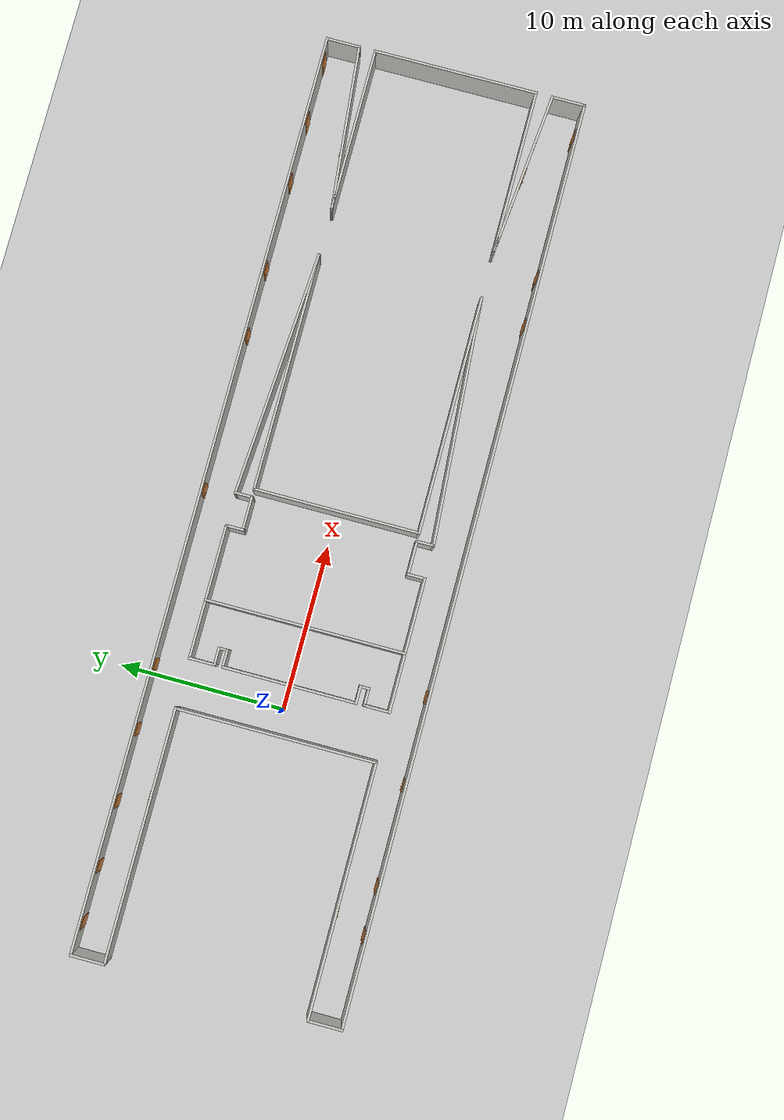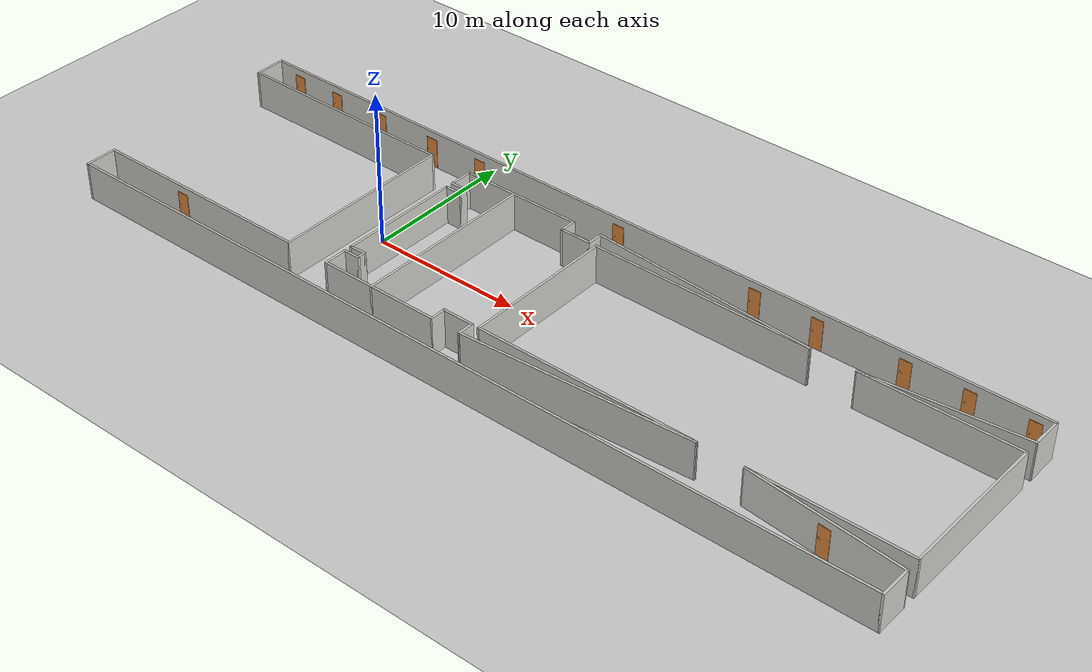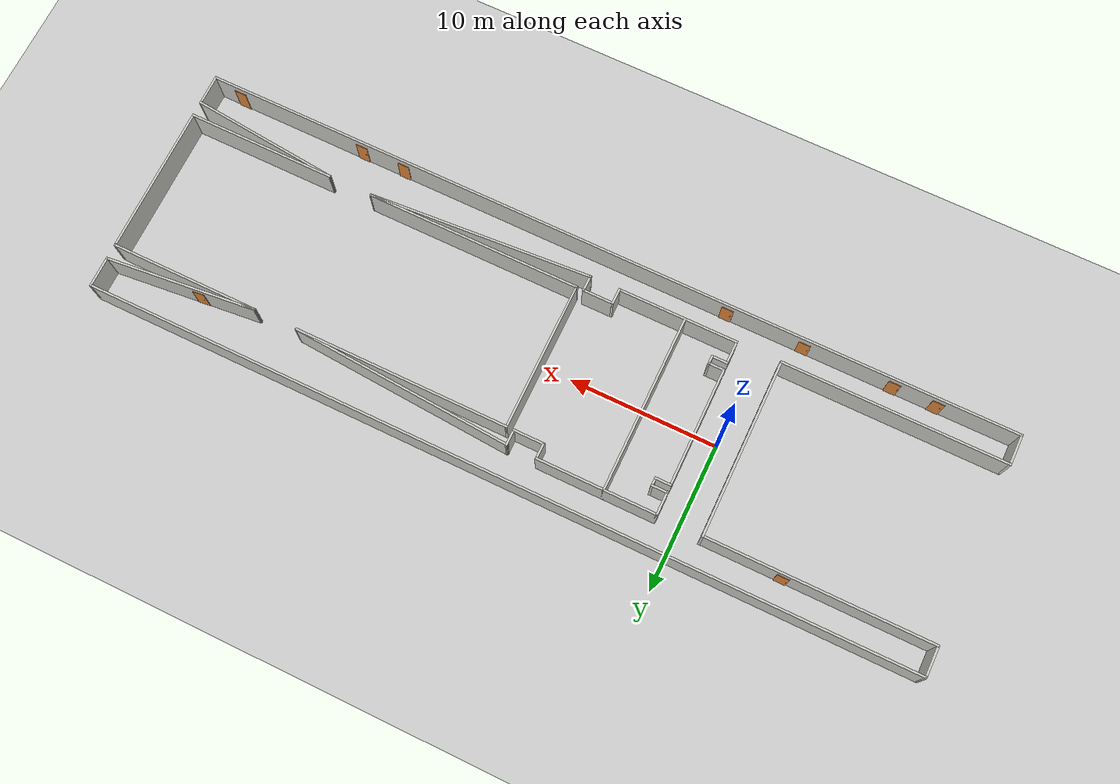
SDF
<sdf version="1.6">
 <world name="default">
  <light name="sun" type="directional">
   <pose>0 0 10 0 -0 0</pose>
   <diffuse>0.8 0.8 0.8 1</diffuse>
   <specular>0.2 0.2 0.2 1</specular>
   <attenuation>
    <range>1000</range>
    <constant>0.9</constant>
    <linear>0.01</linear>
    <quadratic>0.001</quadratic>
   </attenuation>
   <direction>-0.5 0.1 -0.9</direction>
  </light>
  <model name="ground_plane">
   <static>1</static>
   <link name="link">
    <collision name="collision">
     <geometry><plane><normal>0 0 1</normal><size>100 100</size></plane></geometry>
     <surface>
      <contact><collide_bitmask>65535</collide_bitmask></contact>
      <friction><ode><mu>100</mu><mu2>50</mu2></ode></friction>
     </surface>
    </collision>
    <visual name="visual">
     <cast_shadows>0</cast_shadows>
     <geometry><plane><normal>0 0 1</normal><size>100 100</size></plane></geometry>
     <material>
      <script><uri>file://media/materials/scripts/gazebo.material</uri><name>Gazebo/Grey</name></script>
     </material>
    </visual>
   </link>
  </model>
  <gravity>0 0 -9.8</gravity>
  <magnetic_field>6e-06 2.3e-05 -4.2e-05</magnetic_field>
  <atmosphere type="adiabatic"/>
  <physics name="default_physics" default="0" type="ode">
   <max_step_size>0.001</max_step_size>
   <real_time_factor>1</real_time_factor>
   <real_time_update_rate>1000</real_time_update_rate>
  </physics>
  <scene><ambient>0.4 0.4 0.4 1</ambient><background>0.7 0.7 0.7 1</background><shadows>1</shadows></scene>
  <audio><device>default</device></audio>
  <spherical_coordinates>
   <surface_model>EARTH_WGS84</surface_model>
   <latitude_deg>0</latitude_deg>
   <longitude_deg>0</longitude_deg>
   <elevation>0</elevation>
   <heading_deg>0</heading_deg>
  </spherical_coordinates>
  <model name="NURI_3rd">
   <pose>11.5035 0 0 0 -0 0</pose>
   <link name="Wall_0">
    <collision name="Wall_0_Collision">
     <geometry><box><size>56.15 0.15 2.5</size></box></geometry>
     <pose>0 0 1.25 0 -0 0</pose>
    </collision>
    <visual name="Wall_0_Visual">
     <pose>0 0 1.25 0 -0 0</pose>
     <geometry><box><size>56.15 0.15 2.5</size></box></geometry>
     <material>
      <script><uri>file://media/materials/scripts/gazebo.material</uri><name>Gazebo/CeilingTiled</name></script>
      <ambient>1 1 1 1</ambient>
     </material>
     <meta><layer>0</layer></meta>
    </visual>
    <pose>-0.003546 -8 0 0 -0 0</pose>
   </link>
   <link name="Wall_10">
    <collision name="Wall_10_Collision">
     <geometry><box><size>2.15 0.15 2.5</size></box></geometry>
     <pose>0 0 1.25 0 -0 0</pose>
    </collision>
    <visual name="Wall_10_Visual">
     <pose>0 0 1.25 0 -0 0</pose>
     <geometry><box><size>2.15 0.15 2.5</size></box></geometry>
     <material>
      <script><uri>file://media/materials/scripts/gazebo.material</uri><name>Gazebo/CeilingTiled</name></script>
      <ambient>1 1 1 1</ambient>
     </material>
     <meta><layer>0</layer></meta>
    </visual>
    <pose>-28.0035 7 0 0 -0 1.5708</pose>
   </link>
   <link name="Wall_12">
    <collision name="Wall_12_Collision">
     <geometry><box><size>56.15 0.15 2.5</size></box></geometry>
     <pose>0 0 1.25 0 -0 0</pose>
    </collision>
    <visual name="Wall_12_Visual">
     <pose>0 0 1.25 0 -0 0</pose>
     <geometry><box><size>56.15 0.15 2.5</size></box></geometry>
     <material>
      <script><uri>file://media/materials/scripts/gazebo.material</uri><name>Gazebo/CeilingTiled</name></script>
      <ambient>1 1 1 1</ambient>
     </material>
     <meta><layer>0</layer></meta>
    </visual>
    <pose>-0.003546 8 0 0 -0 0</pose>
   </link>
   <link name="Wall_14">
    <collision name="Wall_14_Collision">
     <geometry><box><size>8.15 0.15 2.5</size></box></geometry>
     <pose>0 0 1.25 0 -0 0</pose>
    </collision>
    <visual name="Wall_14_Visual">
     <pose>0 0 1.25 0 -0 0</pose>
     <geometry><box><size>8.15 0.15 2.5</size></box></geometry>
     <material>
      <script><uri>file://media/materials/scripts/gazebo.material</uri><name>Gazebo/CeilingTiled</name></script>
      <ambient>1 1 1 1</ambient>
     </material>
     <meta><layer>0</layer></meta>
    </visual>
    <pose>-6.00355 6 0 0 -0 0</pose>
   </link>
   <link name="Wall_16">
    <collision name="Wall_16_Collision">
     <geometry><box><size>1.65 0.15 2.5</size></box></geometry>
     <pose>0 0 1.25 0 -0 0</pose>
    </collision>
    <visual name="Wall_16_Visual">
     <pose>0 0 1.25 0 -0 0</pose>
     <geometry><box><size>1.65 0.15 2.5</size></box></geometry>
     <material>
      <script><uri>file://media/materials/scripts/gazebo.material</uri><name>Gazebo/CeilingTiled</name></script>
      <ambient>1 1 1 1</ambient>
     </material>
     <meta><layer>0</layer></meta>
    </visual>
    <pose>-10.0035 5.25 0 0 -0 -1.5708</pose>
   </link>
   <link name="Wall_18">
    <collision name="Wall_18_Collision">
     <geometry><box><size>1.15 0.15 2.5</size></box></geometry>
     <pose>0 0 1.25 0 -0 0</pose>
    </collision>
    <visual name="Wall_18_Visual">
     <pose>0 0 1.25 0 -0 0</pose>
     <geometry><box><size>1.15 0.15 2.5</size></box></geometry>
     <material>
      <script><uri>file://media/materials/scripts/gazebo.material</uri><name>Gazebo/CeilingTiled</name></script>
      <ambient>1 1 1 1</ambient>
     </material>
     <meta><layer>0</layer></meta>
    </visual>
    <pose>-9.50355 4.5 0 0 -0 0</pose>
   </link>
   <link name="Wall_2">
    <collision name="Wall_2_Collision">
     <geometry><box><size>2.15 0.15 2.5</size></box></geometry>
     <pose>0 0 1.25 0 -0 0</pose>
    </collision>
    <visual name="Wall_2_Visual">
     <pose>0 0 1.25 0 -0 0</pose>
     <geometry><box><size>2.15 0.15 2.5</size></box></geometry>
     <material>
      <script><uri>file://media/materials/scripts/gazebo.material</uri><name>Gazebo/CeilingTiled</name></script>
      <ambient>1 1 1 1</ambient>
     </material>
     <meta><layer>0</layer></meta>
    </visual>
    <pose>-28.0035 -7 0 0 -0 -1.5708</pose>
   </link>
   <link name="Wall_20">
    <collision name="Wall_20_Collision">
     <geometry><box><size>0.65 0.15 2.5</size></box></geometry>
     <pose>0 0 1.25 0 -0 0</pose>
    </collision>
    <visual name="Wall_20_Visual">
     <pose>0 0 1.25 0 -0 0</pose>
     <geometry><box><size>0.65 0.15 2.5</size></box></geometry>
     <material>
      <script><uri>file://media/materials/scripts/gazebo.material</uri><name>Gazebo/CeilingTiled</name></script>
      <ambient>1 1 1 1</ambient>
     </material>
     <meta><layer>0</layer></meta>
    </visual>
    <pose>-9.00355 4.25 0 0 -0 -1.5708</pose>
   </link>
   <link name="Wall_22">
    <collision name="Wall_22_Collision">
     <geometry><box><size>1.15 0.15 2.5</size></box></geometry>
     <pose>0 0 1.25 0 -0 0</pose>
    </collision>
    <visual name="Wall_22_Visual">
     <pose>0 0 1.25 0 -0 0</pose>
     <geometry><box><size>1.15 0.15 2.5</size></box></geometry>
     <material>
      <script><uri>file://media/materials/scripts/gazebo.material</uri><name>Gazebo/CeilingTiled</name></script>
      <ambient>1 1 1 1</ambient>
     </material>
     <meta><layer>0</layer></meta>
    </visual>
    <pose>-9.50355 4 0 0 -0 3.14159</pose>
   </link>
   <link name="Wall_24">
    <collision name="Wall_24_Collision">
     <geometry><box><size>8.15 0.15 2.5</size></box></geometry>
     <pose>0 0 1.25 0 -0 0</pose>
    </collision>
    <visual name="Wall_24_Visual">
     <pose>0 0 1.25 0 -0 0</pose>
     <geometry><box><size>8.15 0.15 2.5</size></box></geometry>
     <material>
      <script><uri>file://media/materials/scripts/gazebo.material</uri><name>Gazebo/CeilingTiled</name></script>
      <ambient>1 1 1 1</ambient>
     </material>
     <meta><layer>0</layer></meta>
    </visual>
    <pose>-10.0035 0 0 0 -0 -1.5708</pose>
   </link>
   <link name="Wall_26">
    <collision name="Wall_26_Collision">
     <geometry><box><size>1.15 0.15 2.5</size></box></geometry>
     <pose>0 0 1.25 0 -0 0</pose>
    </collision>
    <visual name="Wall_26_Visual">
     <pose>0 0 1.25 0 -0 0</pose>
     <geometry><box><size>1.15 0.15 2.5</size></box></geometry>
     <material>
      <script><uri>file://media/materials/scripts/gazebo.material</uri><name>Gazebo/CeilingTiled</name></script>
      <ambient>1 1 1 1</ambient>
     </material>
     <meta><layer>0</layer></meta>
    </visual>
    <pose>-9.50355 -4 0 0 -0 0</pose>
   </link>
   <link name="Wall_28">
    <collision name="Wall_28_Collision">
     <geometry><box><size>0.65 0.15 2.5</size></box></geometry>
     <pose>0 0 1.25 0 -0 0</pose>
    </collision>
    <visual name="Wall_28_Visual">
     <pose>0 0 1.25 0 -0 0</pose>
     <geometry><box><size>0.65 0.15 2.5</size></box></geometry>
     <material>
      <script><uri>file://media/materials/scripts/gazebo.material</uri><name>Gazebo/CeilingTiled</name></script>
      <ambient>1 1 1 1</ambient>
     </material>
     <meta><layer>0</layer></meta>
    </visual>
    <pose>-9.00355 -4.25 0 0 -0 -1.5708</pose>
   </link>
   <link name="Wall_30">
    <collision name="Wall_30_Collision">
     <geometry><box><size>1.15 0.15 2.5</size></box></geometry>
     <pose>0 0 1.25 0 -0 0</pose>
    </collision>
    <visual name="Wall_30_Visual">
     <pose>0 0 1.25 0 -0 0</pose>
     <geometry><box><size>1.15 0.15 2.5</size></box></geometry>
     <material>
      <script><uri>file://media/materials/scripts/gazebo.material</uri><name>Gazebo/CeilingTiled</name></script>
      <ambient>1 1 1 1</ambient>
     </material>
     <meta><layer>0</layer></meta>
    </visual>
    <pose>-9.50355 -4.5 0 0 -0 3.14159</pose>
   </link>
   <link name="Wall_32">
    <collision name="Wall_32_Collision">
     <geometry><box><size>1.65 0.15 2.5</size></box></geometry>
     <pose>0 0 1.25 0 -0 0</pose>
    </collision>
    <visual name="Wall_32_Visual">
     <pose>0 0 1.25 0 -0 0</pose>
     <geometry><box><size>1.65 0.15 2.5</size></box></geometry>
     <material>
      <script><uri>file://media/materials/scripts/gazebo.material</uri><name>Gazebo/CeilingTiled</name></script>
      <ambient>1 1 1 1</ambient>
     </material>
     <meta><layer>0</layer></meta>
    </visual>
    <pose>-10.0035 -5.25 0 0 -0 -1.5708</pose>
   </link>
   <link name="Wall_34">
    <collision name="Wall_34_Collision">
     <geometry><box><size>8.15 0.15 2.5</size></box></geometry>
     <pose>0 0 1.25 0 -0 0</pose>
    </collision>
    <visual name="Wall_34_Visual">
     <pose>0 0 1.25 0 -0 0</pose>
     <geometry><box><size>8.15 0.15 2.5</size></box></geometry>
     <material>
      <script><uri>file://media/materials/scripts/gazebo.material</uri><name>Gazebo/CeilingTiled</name></script>
      <ambient>1 1 1 1</ambient>
     </material>
     <meta><layer>0</layer></meta>
    </visual>
    <pose>-6.00355 -6 0 0 -0 0</pose>
   </link>
   <link name="Wall_36">
    <collision name="Wall_36_Collision">
     <geometry><box><size>1.15 0.15 2.5</size></box></geometry>
     <pose>0 0 1.25 0 -0 0</pose>
    </collision>
    <visual name="Wall_36_Visual">
     <pose>0 0 1.25 0 -0 0</pose>
     <geometry><box><size>1.15 0.15 2.5</size></box></geometry>
     <material>
      <script><uri>file://media/materials/scripts/gazebo.material</uri><name>Gazebo/CeilingTiled</name></script>
      <ambient>1 1 1 1</ambient>
     </material>
     <meta><layer>0</layer></meta>
    </visual>
    <pose>-2.00355 -5.5 0 0 -0 1.5708</pose>
   </link>
   <link name="Wall_38">
    <collision name="Wall_38_Collision">
     <geometry><box><size>2.15 0.15 2.5</size></box></geometry>
     <pose>0 0 1.25 0 -0 0</pose>
    </collision>
    <visual name="Wall_38_Visual">
     <pose>0 0 1.25 0 -0 0</pose>
     <geometry><box><size>2.15 0.15 2.5</size></box></geometry>
     <material>
      <script><uri>file://media/materials/scripts/gazebo.material</uri><name>Gazebo/CeilingTiled</name></script>
      <ambient>1 1 1 1</ambient>
     </material>
     <meta><layer>0</layer></meta>
    </visual>
    <pose>-1.00355 -5 0 0 -0 0</pose>
   </link>
   <link name="Wall_4">
    <collision name="Wall_4_Collision">
     <geometry><box><size>15.15 0.15 2.5</size></box></geometry>
     <pose>0 0 1.25 0 -0 0</pose>
    </collision>
    <visual name="Wall_4_Visual">
     <pose>0 0 1.25 0 -0 0</pose>
     <geometry><box><size>15.15 0.15 2.5</size></box></geometry>
     <material>
      <script><uri>file://media/materials/scripts/gazebo.material</uri><name>Gazebo/CeilingTiled</name></script>
      <ambient>1 1 1 1</ambient>
     </material>
     <meta><layer>0</layer></meta>
    </visual>
    <pose>-20.5035 -6 0 0 -0 0</pose>
   </link>
   <link name="Wall_40">
    <collision name="Wall_40_Collision">
     <geometry><box><size>1.15 0.15 2.5</size></box></geometry>
     <pose>0 0 1.25 0 -0 0</pose>
    </collision>
    <visual name="Wall_40_Visual">
     <pose>0 0 1.25 0 -0 0</pose>
     <geometry><box><size>1.15 0.15 2.5</size></box></geometry>
     <material>
      <script><uri>file://media/materials/scripts/gazebo.material</uri><name>Gazebo/CeilingTiled</name></script>
      <ambient>1 1 1 1</ambient>
     </material>
     <meta><layer>0</layer></meta>
    </visual>
    <pose>-0.003546 -5.5 0 0 -0 -1.5708</pose>
   </link>
   <link name="Wall_42">
    <collision name="Wall_42_Collision">
     <geometry><box><size>15.1833 0.15 2.5</size></box></geometry>
     <pose>0 0 1.25 0 -0 0</pose>
    </collision>
    <visual name="Wall_42_Visual">
     <pose>0 0 1.25 0 -0 0</pose>
     <geometry><box><size>15.1833 0.15 2.5</size></box></geometry>
     <material>
      <script><uri>file://media/materials/scripts/gazebo.material</uri><name>Gazebo/CeilingTiled</name></script>
      <ambient>1 1 1 1</ambient>
     </material>
     <meta><layer>0</layer></meta>
    </visual>
    <pose>7.49645 -5.5 0 0 -0 0.066568</pose>
   </link>
   <link name="Wall_44">
    <collision name="Wall_44_Collision">
     <geometry><box><size>14.65 0.15 2.5</size></box></geometry>
     <pose>0 0 1.25 0 -0 0</pose>
    </collision>
    <visual name="Wall_44_Visual">
     <pose>0 0 1.25 0 -0 0</pose>
     <geometry><box><size>14.65 0.15 2.5</size></box></geometry>
     <material>
      <script><uri>file://media/materials/scripts/gazebo.material</uri><name>Gazebo/CeilingTiled</name></script>
      <ambient>1 1 1 1</ambient>
     </material>
     <meta><layer>0</layer></meta>
    </visual>
    <pose>7.74645 -5 0 0 -0 3.14159</pose>
   </link>
   <link name="Wall_46">
    <collision name="Wall_46_Collision">
     <geometry><box><size>10.15 0.15 2.5</size></box></geometry>
     <pose>0 0 1.25 0 -0 0</pose>
    </collision>
    <visual name="Wall_46_Visual">
     <pose>0 0 1.25 0 -0 0</pose>
     <geometry><box><size>10.15 0.15 2.5</size></box></geometry>
     <material>
      <script><uri>file://media/materials/scripts/gazebo.material</uri><name>Gazebo/CeilingTiled</name></script>
      <ambient>1 1 1 1</ambient>
     </material>
     <meta><layer>0</layer></meta>
    </visual>
    <pose>0.496454 0 0 0 -0 1.5708</pose>
   </link>
   <link name="Wall_48">
    <collision name="Wall_48_Collision">
     <geometry><box><size>1.15 0.15 2.5</size></box></geometry>
     <pose>0 0 1.25 0 -0 0</pose>
    </collision>
    <visual name="Wall_48_Visual">
     <pose>0 0 1.25 0 -0 0</pose>
     <geometry><box><size>1.15 0.15 2.5</size></box></geometry>
     <material>
      <script><uri>file://media/materials/scripts/gazebo.material</uri><name>Gazebo/CeilingTiled</name></script>
      <ambient>1 1 1 1</ambient>
     </material>
     <meta><layer>0</layer></meta>
    </visual>
    <pose>-2.00355 5.5 0 0 -0 -1.5708</pose>
   </link>
   <link name="Wall_50">
    <collision name="Wall_50_Collision">
     <geometry><box><size>2.15 0.15 2.5</size></box></geometry>
     <pose>0 0 1.25 0 -0 0</pose>
    </collision>
    <visual name="Wall_50_Visual">
     <pose>0 0 1.25 0 -0 0</pose>
     <geometry><box><size>2.15 0.15 2.5</size></box></geometry>
     <material>
      <script><uri>file://media/materials/scripts/gazebo.material</uri><name>Gazebo/CeilingTiled</name></script>
      <ambient>1 1 1 1</ambient>
     </material>
     <meta><layer>0</layer></meta>
    </visual>
    <pose>-1.00355 5 0 0 -0 0</pose>
   </link>
   <link name="Wall_52">
    <collision name="Wall_52_Collision">
     <geometry><box><size>1.15 0.15 2.5</size></box></geometry>
     <pose>0 0 1.25 0 -0 0</pose>
    </collision>
    <visual name="Wall_52_Visual">
     <pose>0 0 1.25 0 -0 0</pose>
     <geometry><box><size>1.15 0.15 2.5</size></box></geometry>
     <material>
      <script><uri>file://media/materials/scripts/gazebo.material</uri><name>Gazebo/CeilingTiled</name></script>
      <ambient>1 1 1 1</ambient>
     </material>
     <meta><layer>0</layer></meta>
    </visual>
    <pose>-0.003546 5.5 0 0 -0 1.5708</pose>
   </link>
   <link name="Wall_54">
    <collision name="Wall_54_Collision">
     <geometry><box><size>15.1833 0.15 2.5</size></box></geometry>
     <pose>0 0 1.25 0 -0 0</pose>
    </collision>
    <visual name="Wall_54_Visual">
     <pose>0 0 1.25 0 -0 0</pose>
     <geometry><box><size>15.1833 0.15 2.5</size></box></geometry>
     <material>
      <script><uri>file://media/materials/scripts/gazebo.material</uri><name>Gazebo/CeilingTiled</name></script>
      <ambient>1 1 1 1</ambient>
     </material>
     <meta><layer>0</layer></meta>
    </visual>
    <pose>7.49645 5.5 0 0 -0 -0.066568</pose>
   </link>
   <link name="Wall_56">
    <collision name="Wall_56_Collision">
     <geometry><box><size>14.65 0.15 2.5</size></box></geometry>
     <pose>0 0 1.25 0 -0 0</pose>
    </collision>
    <visual name="Wall_56_Visual">
     <pose>0 0 1.25 0 -0 0</pose>
     <geometry><box><size>14.65 0.15 2.5</size></box></geometry>
     <material>
      <script><uri>file://media/materials/scripts/gazebo.material</uri><name>Gazebo/CeilingTiled</name></script>
      <ambient>1 1 1 1</ambient>
     </material>
     <meta><layer>0</layer></meta>
    </visual>
    <pose>7.74645 5 0 0 -0 0</pose>
   </link>
   <link name="Wall_58">
    <collision name="Wall_58_Collision">
     <geometry><box><size>10.1999 0.15 2.5</size></box></geometry>
     <pose>0 0 1.25 0 -0 0</pose>
    </collision>
    <visual name="Wall_58_Visual">
     <pose>0 0 1.25 0 -0 0</pose>
     <geometry><box><size>10.1999 0.15 2.5</size></box></geometry>
     <material>
      <script><uri>file://media/materials/scripts/gazebo.material</uri><name>Gazebo/CeilingTiled</name></script>
      <ambient>1 1 1 1</ambient>
     </material>
     <meta><layer>0</layer></meta>
    </visual>
    <pose>22.9965 5.5 0 0 -0 0.099669</pose>
   </link>
   <link name="Wall_6">
    <collision name="Wall_6_Collision">
     <geometry><box><size>12.15 0.15 2.5</size></box></geometry>
     <pose>0 0 1.25 0 -0 0</pose>
    </collision>
    <visual name="Wall_6_Visual">
     <pose>0 0 1.25 0 -0 0</pose>
     <geometry><box><size>12.15 0.15 2.5</size></box></geometry>
     <material>
      <script><uri>file://media/materials/scripts/gazebo.material</uri><name>Gazebo/CeilingTiled</name></script>
      <ambient>1 1 1 1</ambient>
     </material>
     <meta><layer>0</layer></meta>
    </visual>
    <pose>-13.0035 0 0 0 -0 1.5708</pose>
   </link>
   <link name="Wall_60">
    <collision name="Wall_60_Collision">
     <geometry><box><size>2.15 0.15 2.5</size></box></geometry>
     <pose>0 0 1.25 0 -0 0</pose>
    </collision>
    <visual name="Wall_60_Visual">
     <pose>0 0 1.25 0 -0 0</pose>
     <geometry><box><size>2.15 0.15 2.5</size></box></geometry>
     <material>
      <script><uri>file://media/materials/scripts/gazebo.material</uri><name>Gazebo/CeilingTiled</name></script>
      <ambient>1 1 1 1</ambient>
     </material>
     <meta><layer>0</layer></meta>
    </visual>
    <pose>27.9965 7 0 0 -0 -1.5708</pose>
   </link>
   <link name="Wall_62">
    <collision name="Wall_62_Collision">
     <geometry><box><size>2.15 0.15 2.5</size></box></geometry>
     <pose>0 0 1.25 0 -0 0</pose>
    </collision>
    <visual name="Wall_62_Visual">
     <pose>0 0 1.25 0 -0 0</pose>
     <geometry><box><size>2.15 0.15 2.5</size></box></geometry>
     <material>
      <script><uri>file://media/materials/scripts/gazebo.material</uri><name>Gazebo/CeilingTiled</name></script>
      <ambient>1 1 1 1</ambient>
     </material>
     <meta><layer>0</layer></meta>
    </visual>
    <pose>27.9965 -7 0 0 -0 1.5708</pose>
   </link>
   <link name="Wall_64">
    <collision name="Wall_64_Collision">
     <geometry><box><size>10.1999 0.15 2.5</size></box></geometry>
     <pose>0 0 1.25 0 -0 0</pose>
    </collision>
    <visual name="Wall_64_Visual">
     <pose>0 0 1.25 0 -0 0</pose>
     <geometry><box><size>10.1999 0.15 2.5</size></box></geometry>
     <material>
      <script><uri>file://media/materials/scripts/gazebo.material</uri><name>Gazebo/CeilingTiled</name></script>
      <ambient>1 1 1 1</ambient>
     </material>
     <meta><layer>0</layer></meta>
    </visual>
    <pose>22.9965 -5.5 0 0 -0 -0.099669</pose>
   </link>
   <link name="Wall_66">
    <collision name="Wall_66_Collision">
     <geometry><box><size>10.15 0.15 2.5</size></box></geometry>
     <pose>0 0 1.25 0 -0 0</pose>
    </collision>
    <visual name="Wall_66_Visual">
     <pose>0 0 1.25 0 -0 0</pose>
     <geometry><box><size>10.15 0.15 2.5</size></box></geometry>
     <material>
      <script><uri>file://media/materials/scripts/gazebo.material</uri><name>Gazebo/CeilingTiled</name></script>
      <ambient>1 1 1 1</ambient>
     </material>
     <meta><layer>0</layer></meta>
    </visual>
    <pose>22.9965 -5 0 0 -0 0</pose>
   </link>
   <link name="Wall_68">
    <collision name="Wall_68_Collision">
     <geometry><box><size>10.15 0.15 2.5</size></box></geometry>
     <pose>0 0 1.25 0 -0 0</pose>
    </collision>
    <visual name="Wall_68_Visual">
     <pose>0 0 1.25 0 -0 0</pose>
     <geometry><box><size>10.15 0.15 2.5</size></box></geometry>
     <material>
      <script><uri>file://media/materials/scripts/gazebo.material</uri><name>Gazebo/CeilingTiled</name></script>
      <ambient>1 1 1 1</ambient>
     </material>
     <meta><layer>0</layer></meta>
    </visual>
    <pose>22.9965 5 0 0 -0 0</pose>
   </link>
   <link name="Wall_70">
    <collision name="Wall_70_Collision">
     <geometry><box><size>10.15 0.15 2.5</size></box></geometry>
     <pose>0 0 1.25 0 -0 0</pose>
    </collision>
    <visual name="Wall_70_Visual">
     <pose>0 0 1.25 0 -0 0</pose>
     <geometry><box><size>10.15 0.15 2.5</size></box></geometry>
     <material>
      <script><uri>file://media/materials/scripts/gazebo.material</uri><name>Gazebo/CeilingTiled</name></script>
      <ambient>1 1 1 1</ambient>
     </material>
     <meta><layer>0</layer></meta>
    </visual>
    <pose>27.9965 0 0 0 -0 -1.5708</pose>
   </link>
   <link name="Wall_72">
    <collision name="Wall_72_Collision">
     <geometry><box><size>12.15 0.15 2.5</size></box></geometry>
     <pose>0 0 1.25 0 -0 0</pose>
    </collision>
    <visual name="Wall_72_Visual">
     <pose>0 0 1.25 0 -0 0</pose>
     <geometry><box><size>12.15 0.15 2.5</size></box></geometry>
     <material>
      <script><uri>file://media/materials/scripts/gazebo.material</uri><name>Gazebo/CeilingTiled</name></script>
      <ambient>1 1 1 1</ambient>
     </material>
     <meta><layer>0</layer></meta>
    </visual>
    <pose>-6.50355 0 0 0 -0 -1.5708</pose>
   </link>
   <link name="Wall_8">
    <collision name="Wall_8_Collision">
     <geometry><box><size>15.15 0.15 2.5</size></box></geometry>
     <pose>0 0 1.25 0 -0 0</pose>
    </collision>
    <visual name="Wall_8_Visual">
     <pose>0 0 1.25 0 -0 0</pose>
     <geometry><box><size>15.15 0.15 2.5</size></box></geometry>
     <material>
      <script><uri>file://media/materials/scripts/gazebo.material</uri><name>Gazebo/CeilingTiled</name></script>
      <ambient>1 1 1 1</ambient>
     </material>
     <meta><layer>0</layer></meta>
    </visual>
    <pose>-20.5035 6 0 0 -0 3.14159</pose>
   </link>
   <static>1</static>
  </model>
  <model name="door_stand">
   <model name="door">
    <link name="link_0">
     <inertial>
      <mass>1</mass>
      <inertia>
       <ixx>0.166667</ixx>
       <ixy>0</ixy>
       <ixz>0</ixz>
       <iyy>0.166667</iyy>
       <iyz>0</iyz>
       <izz>0.166667</izz>
      </inertia>
     </inertial>
     <visual name="visual">
      <geometry>
       <mesh><uri>/home/msjun-xavier/Downloads/door_C.obj</uri><scale>0.002 0.002 0.001</scale></mesh>
      </geometry>
      <material>
       <lighting>1</lighting>
       <script><uri>file://media/materials/scripts/gazebo.material</uri><name>Gazebo/Grey</name></script>
       <shader type="vertex"><normal_map>__default__</normal_map></shader>
       <ambient>0.875 0.533 0.239 1</ambient>
       <diffuse>0.7 0.7 0.7 1</diffuse>
       <specular>0.01 0.01 0.01 1</specular>
       <emissive>0 0 0 1</emissive>
      </material>
     </visual>
     <collision name="collision">
      <geometry>
       <mesh><uri>/home/msjun-xavier/Downloads/door_C.obj</uri><scale>0.002 0.002 0.001</scale></mesh>
      </geometry>
      <surface>
       <friction>
        <ode><mu>1</mu><mu2>1</mu2><fdir1>0 0 0</fdir1><slip1>0</slip1><slip2>0</slip2></ode>
        <torsional>
         <coefficient>1</coefficient>
         <patch_radius>0</patch_radius>
         <surface_radius>0</surface_radius>
         <use_patch_radius>1</use_patch_radius>
         <ode><slip>0</slip></ode>
        </torsional>
       </friction>
       <bounce><restitution_coefficient>0</restitution_coefficient><threshold>1e+06</threshold></bounce>
       <contact>
        <collide_without_contact>0</collide_without_contact>
        <collide_without_contact_bitmask>1</collide_without_contact_bitmask>
        <collide_bitmask>1</collide_bitmask>
        <ode>
         <soft_cfm>0</soft_cfm>
         <soft_erp>0.2</soft_erp>
         <kp>1e+13</kp>
         <kd>1</kd>
         <max_vel>0.01</max_vel>
         <min_depth>0</min_depth>
        </ode>
        <bullet>
         <split_impulse>1</split_impulse>
         <split_impulse_penetration_threshold>-0.01</split_impulse_penetration_threshold>
         <soft_cfm>0</soft_cfm>
         <soft_erp>0.2</soft_erp>
         <kp>1e+13</kp>
         <kd>1</kd>
        </bullet>
       </contact>
      </surface>
     </collision>
    </link>
    <static>1</static>
    <pose>1e-06 5e-06 0 3.09892 1.53609 -1.61633</pose>
   </model>
   <static>0</static>
   <pose>-2.48687 -7.98897 1.09365 -0.030316 0.007047 -0.005696</pose>
  </model>
  <model name="door_stand_0">
   <model name="door">
    <link name="link_0">
     <inertial>
      <mass>1</mass>
      <inertia>
       <ixx>0.166667</ixx>
       <ixy>0</ixy>
       <ixz>0</ixz>
       <iyy>0.166667</iyy>
       <iyz>0</iyz>
       <izz>0.166667</izz>
      </inertia>
     </inertial>
     <visual name="visual">
      <geometry>
       <mesh><uri>/home/msjun-xavier/Downloads/door_C.obj</uri><scale>0.002 0.002 0.001</scale></mesh>
      </geometry>
      <material>
       <lighting>1</lighting>
       <script><uri>file://media/materials/scripts/gazebo.material</uri><name>Gazebo/Grey</name></script>
       <shader type="vertex"><normal_map>__default__</normal_map></shader>
       <ambient>0.875 0.533 0.239 1</ambient>
       <diffuse>0.7 0.7 0.7 1</diffuse>
       <specular>0.01 0.01 0.01 1</specular>
       <emissive>0 0 0 1</emissive>
      </material>
     </visual>
     <collision name="collision">
      <geometry>
       <mesh><uri>/home/msjun-xavier/Downloads/door_C.obj</uri><scale>0.002 0.002 0.001</scale></mesh>
      </geometry>
      <surface>
       <friction>
        <ode><mu>1</mu><mu2>1</mu2><fdir1>0 0 0</fdir1><slip1>0</slip1><slip2>0</slip2></ode>
        <torsional>
         <coefficient>1</coefficient>
         <patch_radius>0</patch_radius>
         <surface_radius>0</surface_radius>
         <use_patch_radius>1</use_patch_radius>
         <ode><slip>0</slip></ode>
        </torsional>
       </friction>
       <bounce><restitution_coefficient>0</restitution_coefficient><threshold>1e+06</threshold></bounce>
       <contact>
        <collide_without_contact>0</collide_without_contact>
        <collide_without_contact_bitmask>1</collide_without_contact_bitmask>
        <collide_bitmask>1</collide_bitmask>
        <ode>
         <soft_cfm>0</soft_cfm>
         <soft_erp>0.2</soft_erp>
         <kp>1e+13</kp>
         <kd>1</kd>
         <max_vel>0.01</max_vel>
         <min_depth>0</min_depth>
        </ode>
        <bullet>
         <split_impulse>1</split_impulse>
         <split_impulse_penetration_threshold>-0.01</split_impulse_penetration_threshold>
         <soft_cfm>0</soft_cfm>
         <soft_erp>0.2</soft_erp>
         <kp>1e+13</kp>
         <kd>1</kd>
        </bullet>
       </contact>
      </surface>
     </collision>
    </link>
    <static>1</static>
    <pose>1e-06 5e-06 0 3.09892 1.53609 -1.61633</pose>
   </model>
   <static>0</static>
   <pose>-8.50658 -8 1.08 0 -0 0</pose>
  </model>
  <model name="door_stand_1">
   <model name="door">
    <link name="link_0">
     <inertial>
      <mass>1</mass>
      <inertia>
       <ixx>0.166667</ixx>
       <ixy>0</ixy>
       <ixz>0</ixz>
       <iyy>0.166667</iyy>
       <iyz>0</iyz>
       <izz>0.166667</izz>
      </inertia>
     </inertial>
     <visual name="visual">
      <geometry>
       <mesh><uri>/home/msjun-xavier/Downloads/door_C.obj</uri><scale>0.002 0.002 0.001</scale></mesh>
      </geometry>
      <material>
       <lighting>1</lighting>
       <script><uri>file://media/materials/scripts/gazebo.material</uri><name>Gazebo/Grey</name></script>
       <shader type="vertex"><normal_map>__default__</normal_map></shader>
       <ambient>0.875 0.533 0.239 1</ambient>
       <diffuse>0.7 0.7 0.7 1</diffuse>
       <specular>0.01 0.01 0.01 1</specular>
       <emissive>0 0 0 1</emissive>
      </material>
     </visual>
     <collision name="collision">
      <geometry>
       <mesh><uri>/home/msjun-xavier/Downloads/door_C.obj</uri><scale>0.002 0.002 0.001</scale></mesh>
      </geometry>
      <surface>
       <friction>
        <ode><mu>1</mu><mu2>1</mu2><fdir1>0 0 0</fdir1><slip1>0</slip1><slip2>0</slip2></ode>
        <torsional>
         <coefficient>1</coefficient>
         <patch_radius>0</patch_radius>
         <surface_radius>0</surface_radius>
         <use_patch_radius>1</use_patch_radius>
         <ode><slip>0</slip></ode>
        </torsional>
       </friction>
       <bounce><restitution_coefficient>0</restitution_coefficient><threshold>1e+06</threshold></bounce>
       <contact>
        <collide_without_contact>0</collide_without_contact>
        <collide_without_contact_bitmask>1</collide_without_contact_bitmask>
        <collide_bitmask>1</collide_bitmask>
        <ode>
         <soft_cfm>0</soft_cfm>
         <soft_erp>0.2</soft_erp>
         <kp>1e+13</kp>
         <kd>1</kd>
         <max_vel>0.01</max_vel>
         <min_depth>0</min_depth>
        </ode>
        <bullet>
         <split_impulse>1</split_impulse>
         <split_impulse_penetration_threshold>-0.01</split_impulse_penetration_threshold>
         <soft_cfm>0</soft_cfm>
         <soft_erp>0.2</soft_erp>
         <kp>1e+13</kp>
         <kd>1</kd>
        </bullet>
       </contact>
      </surface>
     </collision>
    </link>
    <static>1</static>
    <pose>1e-06 5e-06 0 3.09892 1.53609 -1.61633</pose>
   </model>
   <static>0</static>
   <pose>-11.4064 -8 1.08 0 -0 0</pose>
  </model>
  <model name="door_stand_2">
   <model name="door">
    <link name="link_0">
     <inertial>
      <mass>1</mass>
      <inertia>
       <ixx>0.166667</ixx>
       <ixy>0</ixy>
       <ixz>0</ixz>
       <iyy>0.166667</iyy>
       <iyz>0</iyz>
       <izz>0.166667</izz>
      </inertia>
     </inertial>
     <visual name="visual">
      <geometry>
       <mesh><uri>/home/msjun-xavier/Downloads/door_C.obj</uri><scale>0.002 0.002 0.001</scale></mesh>
      </geometry>
      <material>
       <lighting>1</lighting>
       <script><uri>file://media/materials/scripts/gazebo.material</uri><name>Gazebo/Grey</name></script>
       <shader type="vertex"><normal_map>__default__</normal_map></shader>
       <ambient>0.875 0.533 0.239 1</ambient>
       <diffuse>0.7 0.7 0.7 1</diffuse>
       <specular>0.01 0.01 0.01 1</specular>
       <emissive>0 0 0 1</emissive>
      </material>
     </visual>
     <collision name="collision">
      <geometry>
       <mesh><uri>/home/msjun-xavier/Downloads/door_C.obj</uri><scale>0.002 0.002 0.001</scale></mesh>
      </geometry>
      <surface>
       <friction>
        <ode><mu>1</mu><mu2>1</mu2><fdir1>0 0 0</fdir1><slip1>0</slip1><slip2>0</slip2></ode>
        <torsional>
         <coefficient>1</coefficient>
         <patch_radius>0</patch_radius>
         <surface_radius>0</surface_radius>
         <use_patch_radius>1</use_patch_radius>
         <ode><slip>0</slip></ode>
        </torsional>
       </friction>
       <bounce><restitution_coefficient>0</restitution_coefficient><threshold>1e+06</threshold></bounce>
       <contact>
        <collide_without_contact>0</collide_without_contact>
        <collide_without_contact_bitmask>1</collide_without_contact_bitmask>
        <collide_bitmask>1</collide_bitmask>
        <ode>
         <soft_cfm>0</soft_cfm>
         <soft_erp>0.2</soft_erp>
         <kp>1e+13</kp>
         <kd>1</kd>
         <max_vel>0.01</max_vel>
         <min_depth>0</min_depth>
        </ode>
        <bullet>
         <split_impulse>1</split_impulse>
         <split_impulse_penetration_threshold>-0.01</split_impulse_penetration_threshold>
         <soft_cfm>0</soft_cfm>
         <soft_erp>0.2</soft_erp>
         <kp>1e+13</kp>
         <kd>1</kd>
        </bullet>
       </contact>
      </surface>
     </collision>
    </link>
    <static>1</static>
    <pose>1e-06 5e-06 0 3.09892 1.53609 -1.61633</pose>
   </model>
   <static>0</static>
   <pose>2.76426 -8 1.08 0 -0 0</pose>
  </model>
  <model name="door_stand_3">
   <model name="door">
    <link name="link_0">
     <inertial>
      <mass>1</mass>
      <inertia>
       <ixx>0.166667</ixx>
       <ixy>0</ixy>
       <ixz>0</ixz>
       <iyy>0.166667</iyy>
       <iyz>0</iyz>
       <izz>0.166667</izz>
      </inertia>
     </inertial>
     <visual name="visual">
      <geometry>
       <mesh><uri>/home/msjun-xavier/Downloads/door_C.obj</uri><scale>0.002 0.002 0.001</scale></mesh>
      </geometry>
      <material>
       <lighting>1</lighting>
       <script><uri>file://media/materials/scripts/gazebo.material</uri><name>Gazebo/Grey</name></script>
       <shader type="vertex"><normal_map>__default__</normal_map></shader>
       <ambient>0.875 0.533 0.239 1</ambient>
       <diffuse>0.7 0.7 0.7 1</diffuse>
       <specular>0.01 0.01 0.01 1</specular>
       <emissive>0 0 0 1</emissive>
      </material>
     </visual>
     <collision name="collision">
      <geometry>
       <mesh><uri>/home/msjun-xavier/Downloads/door_C.obj</uri><scale>0.002 0.002 0.001</scale></mesh>
      </geometry>
      <surface>
       <friction>
        <ode><mu>1</mu><mu2>1</mu2><fdir1>0 0 0</fdir1><slip1>0</slip1><slip2>0</slip2></ode>
        <torsional>
         <coefficient>1</coefficient>
         <patch_radius>0</patch_radius>
         <surface_radius>0</surface_radius>
         <use_patch_radius>1</use_patch_radius>
         <ode><slip>0</slip></ode>
        </torsional>
       </friction>
       <bounce><restitution_coefficient>0</restitution_coefficient><threshold>1e+06</threshold></bounce>
       <contact>
        <collide_without_contact>0</collide_without_contact>
        <collide_without_contact_bitmask>1</collide_without_contact_bitmask>
        <collide_bitmask>1</collide_bitmask>
        <ode>
         <soft_cfm>0</soft_cfm>
         <soft_erp>0.2</soft_erp>
         <kp>1e+13</kp>
         <kd>1</kd>
         <max_vel>0.01</max_vel>
         <min_depth>0</min_depth>
        </ode>
        <bullet>
         <split_impulse>1</split_impulse>
         <split_impulse_penetration_threshold>-0.01</split_impulse_penetration_threshold>
         <soft_cfm>0</soft_cfm>
         <soft_erp>0.2</soft_erp>
         <kp>1e+13</kp>
         <kd>1</kd>
        </bullet>
       </contact>
      </surface>
     </collision>
    </link>
    <static>1</static>
    <pose>1e-06 5e-06 0 3.09892 1.53609 -1.61633</pose>
   </model>
   <static>0</static>
   <pose>25.6173 -8 1.08 0 -0 0</pose>
  </model>
  <model name="door_stand_4">
   <model name="door">
    <link name="link_0">
     <inertial>
      <mass>1</mass>
      <inertia>
       <ixx>0.166667</ixx>
       <ixy>0</ixy>
       <ixz>0</ixz>
       <iyy>0.166667</iyy>
       <iyz>0</iyz>
       <izz>0.166667</izz>
      </inertia>
     </inertial>
     <visual name="visual">
      <geometry>
       <mesh><uri>/home/msjun-xavier/Downloads/door_C.obj</uri><scale>0.002 0.002 0.001</scale></mesh>
      </geometry>
      <material>
       <lighting>1</lighting>
       <script><uri>file://media/materials/scripts/gazebo.material</uri><name>Gazebo/Grey</name></script>
       <shader type="vertex"><normal_map>__default__</normal_map></shader>
       <ambient>0.875 0.533 0.239 1</ambient>
       <diffuse>0.7 0.7 0.7 1</diffuse>
       <specular>0.01 0.01 0.01 1</specular>
       <emissive>0 0 0 1</emissive>
      </material>
     </visual>
     <collision name="collision">
      <geometry>
       <mesh><uri>/home/msjun-xavier/Downloads/door_C.obj</uri><scale>0.002 0.002 0.001</scale></mesh>
      </geometry>
      <surface>
       <friction>
        <ode><mu>1</mu><mu2>1</mu2><fdir1>0 0 0</fdir1><slip1>0</slip1><slip2>0</slip2></ode>
        <torsional>
         <coefficient>1</coefficient>
         <patch_radius>0</patch_radius>
         <surface_radius>0</surface_radius>
         <use_patch_radius>1</use_patch_radius>
         <ode><slip>0</slip></ode>
        </torsional>
       </friction>
       <bounce><restitution_coefficient>0</restitution_coefficient><threshold>1e+06</threshold></bounce>
       <contact>
        <collide_without_contact>0</collide_without_contact>
        <collide_without_contact_bitmask>1</collide_without_contact_bitmask>
        <collide_bitmask>1</collide_bitmask>
        <ode>
         <soft_cfm>0</soft_cfm>
         <soft_erp>0.2</soft_erp>
         <kp>1e+13</kp>
         <kd>1</kd>
         <max_vel>0.01</max_vel>
         <min_depth>0</min_depth>
        </ode>
        <bullet>
         <split_impulse>1</split_impulse>
         <split_impulse_penetration_threshold>-0.01</split_impulse_penetration_threshold>
         <soft_cfm>0</soft_cfm>
         <soft_erp>0.2</soft_erp>
         <kp>1e+13</kp>
         <kd>1</kd>
        </bullet>
       </contact>
      </surface>
     </collision>
    </link>
    <static>1</static>
    <pose>1e-06 5e-06 0 3.09892 1.53609 -1.61633</pose>
   </model>
   <static>0</static>
   <pose>28.6473 -8 1.08 0 -0 0</pose>
  </model>
  <model name="door_stand_5">
   <model name="door">
    <link name="link_0">
     <inertial>
      <mass>1</mass>
      <inertia>
       <ixx>0.166667</ixx>
       <ixy>0</ixy>
       <ixz>0</ixz>
       <iyy>0.166667</iyy>
       <iyz>0</iyz>
       <izz>0.166667</izz>
      </inertia>
     </inertial>
     <visual name="visual">
      <geometry>
       <mesh><uri>/home/msjun-xavier/Downloads/door_C.obj</uri><scale>0.002 0.002 0.001</scale></mesh>
      </geometry>
      <material>
       <lighting>1</lighting>
       <script><uri>file://media/materials/scripts/gazebo.material</uri><name>Gazebo/Grey</name></script>
       <shader type="vertex"><normal_map>__default__</normal_map></shader>
       <ambient>0.875 0.533 0.239 1</ambient>
       <diffuse>0.7 0.7 0.7 1</diffuse>
       <specular>0.01 0.01 0.01 1</specular>
       <emissive>0 0 0 1</emissive>
      </material>
     </visual>
     <collision name="collision">
      <geometry>
       <mesh><uri>/home/msjun-xavier/Downloads/door_C.obj</uri><scale>0.002 0.002 0.001</scale></mesh>
      </geometry>
      <surface>
       <friction>
        <ode><mu>1</mu><mu2>1</mu2><fdir1>0 0 0</fdir1><slip1>0</slip1><slip2>0</slip2></ode>
        <torsional>
         <coefficient>1</coefficient>
         <patch_radius>0</patch_radius>
         <surface_radius>0</surface_radius>
         <use_patch_radius>1</use_patch_radius>
         <ode><slip>0</slip></ode>
        </torsional>
       </friction>
       <bounce><restitution_coefficient>0</restitution_coefficient><threshold>1e+06</threshold></bounce>
       <contact>
        <collide_without_contact>0</collide_without_contact>
        <collide_without_contact_bitmask>1</collide_without_contact_bitmask>
        <collide_bitmask>1</collide_bitmask>
        <ode>
         <soft_cfm>0</soft_cfm>
         <soft_erp>0.2</soft_erp>
         <kp>1e+13</kp>
         <kd>1</kd>
         <max_vel>0.01</max_vel>
         <min_depth>0</min_depth>
        </ode>
        <bullet>
         <split_impulse>1</split_impulse>
         <split_impulse_penetration_threshold>-0.01</split_impulse_penetration_threshold>
         <soft_cfm>0</soft_cfm>
         <soft_erp>0.2</soft_erp>
         <kp>1e+13</kp>
         <kd>1</kd>
        </bullet>
       </contact>
      </surface>
     </collision>
    </link>
    <static>1</static>
    <pose>1e-06 5e-06 0 3.09892 1.53609 -1.61633</pose>
   </model>
   <static>0</static>
   <pose>37.6167 -8 1.08 0 -0 0</pose>
  </model>
  <model name="door_stand_6">
   <model name="door">
    <link name="link_0">
     <inertial>
      <mass>1</mass>
      <inertia>
       <ixx>0.166667</ixx>
       <ixy>0</ixy>
       <ixz>0</ixz>
       <iyy>0.166667</iyy>
       <iyz>0</iyz>
       <izz>0.166667</izz>
      </inertia>
     </inertial>
     <visual name="visual">
      <geometry>
       <mesh><uri>/home/msjun-xavier/Downloads/door_C.obj</uri><scale>0.002 0.002 0.001</scale></mesh>
      </geometry>
      <material>
       <lighting>1</lighting>
       <script><uri>file://media/materials/scripts/gazebo.material</uri><name>Gazebo/Grey</name></script>
       <shader type="vertex"><normal_map>__default__</normal_map></shader>
       <ambient>0.875 0.533 0.239 1</ambient>
       <diffuse>0.7 0.7 0.7 1</diffuse>
       <specular>0.01 0.01 0.01 1</specular>
       <emissive>0 0 0 1</emissive>
      </material>
     </visual>
     <collision name="collision">
      <geometry>
       <mesh><uri>/home/msjun-xavier/Downloads/door_C.obj</uri><scale>0.002 0.002 0.001</scale></mesh>
      </geometry>
      <surface>
       <friction>
        <ode><mu>1</mu><mu2>1</mu2><fdir1>0 0 0</fdir1><slip1>0</slip1><slip2>0</slip2></ode>
        <torsional>
         <coefficient>1</coefficient>
         <patch_radius>0</patch_radius>
         <surface_radius>0</surface_radius>
         <use_patch_radius>1</use_patch_radius>
         <ode><slip>0</slip></ode>
        </torsional>
       </friction>
       <bounce><restitution_coefficient>0</restitution_coefficient><threshold>1e+06</threshold></bounce>
       <contact>
        <collide_without_contact>0</collide_without_contact>
        <collide_without_contact_bitmask>1</collide_without_contact_bitmask>
        <collide_bitmask>1</collide_bitmask>
        <ode>
         <soft_cfm>0</soft_cfm>
         <soft_erp>0.2</soft_erp>
         <kp>1e+13</kp>
         <kd>1</kd>
         <max_vel>0.01</max_vel>
         <min_depth>0</min_depth>
        </ode>
        <bullet>
         <split_impulse>1</split_impulse>
         <split_impulse_penetration_threshold>-0.01</split_impulse_penetration_threshold>
         <soft_cfm>0</soft_cfm>
         <soft_erp>0.2</soft_erp>
         <kp>1e+13</kp>
         <kd>1</kd>
        </bullet>
       </contact>
      </surface>
     </collision>
    </link>
    <static>1</static>
    <pose>1e-06 5e-06 0 3.09892 1.53609 -1.61633</pose>
   </model>
   <static>0</static>
   <pose>33.2654 5.34285 1.08 0 -0 0.106649</pose>
  </model>
  <model name="door_stand_7">
   <model name="door">
    <link name="link_0">
     <inertial>
      <mass>1</mass>
      <inertia>
       <ixx>0.166667</ixx>
       <ixy>0</ixy>
       <ixz>0</ixz>
       <iyy>0.166667</iyy>
       <iyz>0</iyz>
       <izz>0.166667</izz>
      </inertia>
     </inertial>
     <visual name="visual">
      <geometry>
       <mesh><uri>/home/msjun-xavier/Downloads/door_C.obj</uri><scale>0.002 0.002 0.001</scale></mesh>
      </geometry>
      <material>
       <lighting>1</lighting>
       <script><uri>file://media/materials/scripts/gazebo.material</uri><name>Gazebo/Grey</name></script>
       <shader type="vertex"><normal_map>__default__</normal_map></shader>
       <ambient>0.875 0.533 0.239 1</ambient>
       <diffuse>0.7 0.7 0.7 1</diffuse>
       <specular>0.01 0.01 0.01 1</specular>
       <emissive>0 0 0 1</emissive>
      </material>
     </visual>
     <collision name="collision">
      <geometry>
       <mesh><uri>/home/msjun-xavier/Downloads/door_C.obj</uri><scale>0.002 0.002 0.001</scale></mesh>
      </geometry>
      <surface>
       <friction>
        <ode><mu>1</mu><mu2>1</mu2><fdir1>0 0 0</fdir1><slip1>0</slip1><slip2>0</slip2></ode>
        <torsional>
         <coefficient>1</coefficient>
         <patch_radius>0</patch_radius>
         <surface_radius>0</surface_radius>
         <use_patch_radius>1</use_patch_radius>
         <ode><slip>0</slip></ode>
        </torsional>
       </friction>
       <bounce><restitution_coefficient>0</restitution_coefficient><threshold>1e+06</threshold></bounce>
       <contact>
        <collide_without_contact>0</collide_without_contact>
        <collide_without_contact_bitmask>1</collide_without_contact_bitmask>
        <collide_bitmask>1</collide_bitmask>
        <ode>
         <soft_cfm>0</soft_cfm>
         <soft_erp>0.2</soft_erp>
         <kp>1e+13</kp>
         <kd>1</kd>
         <max_vel>0.01</max_vel>
         <min_depth>0</min_depth>
        </ode>
        <bullet>
         <split_impulse>1</split_impulse>
         <split_impulse_penetration_threshold>-0.01</split_impulse_penetration_threshold>
         <soft_cfm>0</soft_cfm>
         <soft_erp>0.2</soft_erp>
         <kp>1e+13</kp>
         <kd>1</kd>
        </bullet>
       </contact>
      </surface>
     </collision>
    </link>
    <static>1</static>
    <pose>1e-06 5e-06 0 3.09892 1.53609 -1.61633</pose>
   </model>
   <static>0</static>
   <pose>-6.94404 6 1.08 0 -0 0</pose>
  </model>
  <model name="door_stand_8">
   <model name="door">
    <link name="link_0">
     <inertial>
      <mass>1</mass>
      <inertia>
       <ixx>0.166667</ixx>
       <ixy>0</ixy>
       <ixz>0</ixz>
       <iyy>0.166667</iyy>
       <iyz>0</iyz>
       <izz>0.166667</izz>
      </inertia>
     </inertial>
     <visual name="visual">
      <geometry>
       <mesh><uri>/home/msjun-xavier/Downloads/door_C.obj</uri><scale>0.002 0.002 0.001</scale></mesh>
      </geometry>
      <material>
       <lighting>1</lighting>
       <script><uri>file://media/materials/scripts/gazebo.material</uri><name>Gazebo/Grey</name></script>
       <shader type="vertex"><normal_map>__default__</normal_map></shader>
       <ambient>0.875 0.533 0.239 1</ambient>
       <diffuse>0.7 0.7 0.7 1</diffuse>
       <specular>0.01 0.01 0.01 1</specular>
       <emissive>0 0 0 1</emissive>
      </material>
     </visual>
     <collision name="collision">
      <geometry>
       <mesh><uri>/home/msjun-xavier/Downloads/door_C.obj</uri><scale>0.002 0.002 0.001</scale></mesh>
      </geometry>
      <surface>
       <friction>
        <ode><mu>1</mu><mu2>1</mu2><fdir1>0 0 0</fdir1><slip1>0</slip1><slip2>0</slip2></ode>
        <torsional>
         <coefficient>1</coefficient>
         <patch_radius>0</patch_radius>
         <surface_radius>0</surface_radius>
         <use_patch_radius>1</use_patch_radius>
         <ode><slip>0</slip></ode>
        </torsional>
       </friction>
       <bounce><restitution_coefficient>0</restitution_coefficient><threshold>1e+06</threshold></bounce>
       <contact>
        <collide_without_contact>0</collide_without_contact>
        <collide_without_contact_bitmask>1</collide_without_contact_bitmask>
        <collide_bitmask>1</collide_bitmask>
        <ode>
         <soft_cfm>0</soft_cfm>
         <soft_erp>0.2</soft_erp>
         <kp>1e+13</kp>
         <kd>1</kd>
         <max_vel>0.01</max_vel>
         <min_depth>0</min_depth>
        </ode>
        <bullet>
         <split_impulse>1</split_impulse>
         <split_impulse_penetration_threshold>-0.01</split_impulse_penetration_threshold>
         <soft_cfm>0</soft_cfm>
         <soft_erp>0.2</soft_erp>
         <kp>1e+13</kp>
         <kd>1</kd>
        </bullet>
       </contact>
      </surface>
     </collision>
    </link>
    <static>1</static>
    <pose>1e-06 5e-06 0 3.09892 1.53609 -1.61633</pose>
   </model>
   <static>0</static>
   <pose>-10.455 -6.2 1.08 0 -0 0</pose>
  </model>
  <model name="door_stand_9">
   <model name="door">
    <link name="link_0">
     <inertial>
      <mass>1</mass>
      <inertia>
       <ixx>0.166667</ixx>
       <ixy>0</ixy>
       <ixz>0</ixz>
       <iyy>0.166667</iyy>
       <iyz>0</iyz>
       <izz>0.166667</izz>
      </inertia>
     </inertial>
     <visual name="visual">
      <geometry>
       <mesh><uri>/home/msjun-xavier/Downloads/door_C.obj</uri><scale>0.002 0.002 0.001</scale></mesh>
      </geometry>
      <material>
       <lighting>1</lighting>
       <script><uri>file://media/materials/scripts/gazebo.material</uri><name>Gazebo/Grey</name></script>
       <shader type="vertex"><normal_map>__default__</normal_map></shader>
       <ambient>0.875 0.533 0.239 1</ambient>
       <diffuse>0.7 0.7 0.7 1</diffuse>
       <specular>0.01 0.01 0.01 1</specular>
       <emissive>0 0 0 1</emissive>
      </material>
     </visual>
     <collision name="collision">
      <geometry>
       <mesh><uri>/home/msjun-xavier/Downloads/door_C.obj</uri><scale>0.002 0.002 0.001</scale></mesh>
      </geometry>
      <surface>
       <friction>
        <ode><mu>1</mu><mu2>1</mu2><fdir1>0 0 0</fdir1><slip1>0</slip1><slip2>0</slip2></ode>
        <torsional>
         <coefficient>1</coefficient>
         <patch_radius>0</patch_radius>
         <surface_radius>0</surface_radius>
         <use_patch_radius>1</use_patch_radius>
         <ode><slip>0</slip></ode>
        </torsional>
       </friction>
       <bounce><restitution_coefficient>0</restitution_coefficient><threshold>1e+06</threshold></bounce>
       <contact>
        <collide_without_contact>0</collide_without_contact>
        <collide_without_contact_bitmask>1</collide_without_contact_bitmask>
        <collide_bitmask>1</collide_bitmask>
        <ode>
         <soft_cfm>0</soft_cfm>
         <soft_erp>0.2</soft_erp>
         <kp>1e+13</kp>
         <kd>1</kd>
         <max_vel>0.01</max_vel>
         <min_depth>0</min_depth>
        </ode>
        <bullet>
         <split_impulse>1</split_impulse>
         <split_impulse_penetration_threshold>-0.01</split_impulse_penetration_threshold>
         <soft_cfm>0</soft_cfm>
         <soft_erp>0.2</soft_erp>
         <kp>1e+13</kp>
         <kd>1</kd>
        </bullet>
       </contact>
      </surface>
     </collision>
    </link>
    <static>1</static>
    <pose>1e-06 5e-06 0 3.09892 1.53609 -1.61633</pose>
   </model>
   <static>0</static>
   <pose>34.5353 -5.70023 1.08 0 0 -0.104588</pose>
  </model>
  <model name="door_stand_10">
   <model name="door">
    <link name="link_0">
     <inertial>
      <mass>1</mass>
      <inertia>
       <ixx>0.166667</ixx>
       <ixy>0</ixy>
       <ixz>0</ixz>
       <iyy>0.166667</iyy>
       <iyz>0</iyz>
       <izz>0.166667</izz>
      </inertia>
     </inertial>
     <visual name="visual">
      <geometry>
       <mesh><uri>/home/msjun-xavier/Downloads/door_C.obj</uri><scale>0.002 0.002 0.001</scale></mesh>
      </geometry>
      <material>
       <lighting>1</lighting>
       <script><uri>file://media/materials/scripts/gazebo.material</uri><name>Gazebo/Grey</name></script>
       <shader type="vertex"><normal_map>__default__</normal_map></shader>
       <ambient>0.875 0.533 0.239 1</ambient>
       <diffuse>0.7 0.7 0.7 1</diffuse>
       <specular>0.01 0.01 0.01 1</specular>
       <emissive>0 0 0 1</emissive>
      </material>
     </visual>
     <collision name="collision">
      <geometry>
       <mesh><uri>/home/msjun-xavier/Downloads/door_C.obj</uri><scale>0.002 0.002 0.001</scale></mesh>
      </geometry>
      <surface>
       <friction>
        <ode><mu>1</mu><mu2>1</mu2><fdir1>0 0 0</fdir1><slip1>0</slip1><slip2>0</slip2></ode>
        <torsional>
         <coefficient>1</coefficient>
         <patch_radius>0</patch_radius>
         <surface_radius>0</surface_radius>
         <use_patch_radius>1</use_patch_radius>
         <ode><slip>0</slip></ode>
        </torsional>
       </friction>
       <bounce><restitution_coefficient>0</restitution_coefficient><threshold>1e+06</threshold></bounce>
       <contact>
        <collide_without_contact>0</collide_without_contact>
        <collide_without_contact_bitmask>1</collide_without_contact_bitmask>
        <collide_bitmask>1</collide_bitmask>
        <ode>
         <soft_cfm>0</soft_cfm>
         <soft_erp>0.2</soft_erp>
         <kp>1e+13</kp>
         <kd>1</kd>
         <max_vel>0.01</max_vel>
         <min_depth>0</min_depth>
        </ode>
        <bullet>
         <split_impulse>1</split_impulse>
         <split_impulse_penetration_threshold>-0.01</split_impulse_penetration_threshold>
         <soft_cfm>0</soft_cfm>
         <soft_erp>0.2</soft_erp>
         <kp>1e+13</kp>
         <kd>1</kd>
        </bullet>
       </contact>
      </surface>
     </collision>
    </link>
    <static>1</static>
    <pose>1e-06 5e-06 0 3.09892 1.53609 -1.61633</pose>
   </model>
   <static>0</static>
   <pose>38.3584 7.8 1.08 0 -0 0</pose>
  </model>
  <model name="door_stand_11">
   <model name="door">
    <link name="link_0">
     <inertial>
      <mass>1</mass>
      <inertia>
       <ixx>0.166667</ixx>
       <ixy>0</ixy>
       <ixz>0</ixz>
       <iyy>0.166667</iyy>
       <iyz>0</iyz>
       <izz>0.166667</izz>
      </inertia>
     </inertial>
     <visual name="visual">
      <geometry>
       <mesh><uri>/home/msjun-xavier/Downloads/door_C.obj</uri><scale>0.002 0.002 0.001</scale></mesh>
      </geometry>
      <material>
       <lighting>1</lighting>
       <script><uri>file://media/materials/scripts/gazebo.material</uri><name>Gazebo/Grey</name></script>
       <shader type="vertex"><normal_map>__default__</normal_map></shader>
       <ambient>0.875 0.533 0.239 1</ambient>
       <diffuse>0.7 0.7 0.7 1</diffuse>
       <specular>0.01 0.01 0.01 1</specular>
       <emissive>0 0 0 1</emissive>
      </material>
     </visual>
     <collision name="collision">
      <geometry>
       <mesh><uri>/home/msjun-xavier/Downloads/door_C.obj</uri><scale>0.002 0.002 0.001</scale></mesh>
      </geometry>
      <surface>
       <friction>
        <ode><mu>1</mu><mu2>1</mu2><fdir1>0 0 0</fdir1><slip1>0</slip1><slip2>0</slip2></ode>
        <torsional>
         <coefficient>1</coefficient>
         <patch_radius>0</patch_radius>
         <surface_radius>0</surface_radius>
         <use_patch_radius>1</use_patch_radius>
         <ode><slip>0</slip></ode>
        </torsional>
       </friction>
       <bounce><restitution_coefficient>0</restitution_coefficient><threshold>1e+06</threshold></bounce>
       <contact>
        <collide_without_contact>0</collide_without_contact>
        <collide_without_contact_bitmask>1</collide_without_contact_bitmask>
        <collide_bitmask>1</collide_bitmask>
        <ode>
         <soft_cfm>0</soft_cfm>
         <soft_erp>0.2</soft_erp>
         <kp>1e+13</kp>
         <kd>1</kd>
         <max_vel>0.01</max_vel>
         <min_depth>0</min_depth>
        </ode>
        <bullet>
         <split_impulse>1</split_impulse>
         <split_impulse_penetration_threshold>-0.01</split_impulse_penetration_threshold>
         <soft_cfm>0</soft_cfm>
         <soft_erp>0.2</soft_erp>
         <kp>1e+13</kp>
         <kd>1</kd>
        </bullet>
       </contact>
      </surface>
     </collision>
    </link>
    <static>1</static>
    <pose>1e-06 5e-06 0 3.09892 1.53609 -1.61633</pose>
   </model>
   <static>0</static>
   <pose>34.5052 7.8 1.08 0 -0 0</pose>
  </model>
  <model name="door_stand_12">
   <model name="door">
    <link name="link_0">
     <inertial>
      <mass>1</mass>
      <inertia>
       <ixx>0.166667</ixx>
       <ixy>0</ixy>
       <ixz>0</ixz>
       <iyy>0.166667</iyy>
       <iyz>0</iyz>
       <izz>0.166667</izz>
      </inertia>
     </inertial>
     <visual name="visual">
      <geometry>
       <mesh><uri>/home/msjun-xavier/Downloads/door_C.obj</uri><scale>0.002 0.002 0.001</scale></mesh>
      </geometry>
      <material>
       <lighting>1</lighting>
       <script><uri>file://media/materials/scripts/gazebo.material</uri><name>Gazebo/Grey</name></script>
       <shader type="vertex"><normal_map>__default__</normal_map></shader>
       <ambient>0.875 0.533 0.239 1</ambient>
       <diffuse>0.7 0.7 0.7 1</diffuse>
       <specular>0.01 0.01 0.01 1</specular>
       <emissive>0 0 0 1</emissive>
      </material>
     </visual>
     <collision name="collision">
      <geometry>
       <mesh><uri>/home/msjun-xavier/Downloads/door_C.obj</uri><scale>0.002 0.002 0.001</scale></mesh>
      </geometry>
      <surface>
       <friction>
        <ode><mu>1</mu><mu2>1</mu2><fdir1>0 0 0</fdir1><slip1>0</slip1><slip2>0</slip2></ode>
        <torsional>
         <coefficient>1</coefficient>
         <patch_radius>0</patch_radius>
         <surface_radius>0</surface_radius>
         <use_patch_radius>1</use_patch_radius>
         <ode><slip>0</slip></ode>
        </torsional>
       </friction>
       <bounce><restitution_coefficient>0</restitution_coefficient><threshold>1e+06</threshold></bounce>
       <contact>
        <collide_without_contact>0</collide_without_contact>
        <collide_without_contact_bitmask>1</collide_without_contact_bitmask>
        <collide_bitmask>1</collide_bitmask>
        <ode>
         <soft_cfm>0</soft_cfm>
         <soft_erp>0.2</soft_erp>
         <kp>1e+13</kp>
         <kd>1</kd>
         <max_vel>0.01</max_vel>
         <min_depth>0</min_depth>
        </ode>
        <bullet>
         <split_impulse>1</split_impulse>
         <split_impulse_penetration_threshold>-0.01</split_impulse_penetration_threshold>
         <soft_cfm>0</soft_cfm>
         <soft_erp>0.2</soft_erp>
         <kp>1e+13</kp>
         <kd>1</kd>
        </bullet>
       </contact>
      </surface>
     </collision>
    </link>
    <static>1</static>
    <pose>1e-06 5e-06 0 3.09892 1.53609 -1.61633</pose>
   </model>
   <static>0</static>
   <pose>30.5792 7.8 1.08 0 -0 0</pose>
  </model>
  <model name="door_stand_13">
   <model name="door">
    <link name="link_0">
     <inertial>
      <mass>1</mass>
      <inertia>
       <ixx>0.166667</ixx>
       <ixy>0</ixy>
       <ixz>0</ixz>
       <iyy>0.166667</iyy>
       <iyz>0</iyz>
       <izz>0.166667</izz>
      </inertia>
     </inertial>
     <visual name="visual">
      <geometry>
       <mesh><uri>/home/msjun-xavier/Downloads/door_C.obj</uri><scale>0.002 0.002 0.001</scale></mesh>
      </geometry>
      <material>
       <lighting>1</lighting>
       <script><uri>file://media/materials/scripts/gazebo.material</uri><name>Gazebo/Grey</name></script>
       <shader type="vertex"><normal_map>__default__</normal_map></shader>
       <ambient>0.875 0.533 0.239 1</ambient>
       <diffuse>0.7 0.7 0.7 1</diffuse>
       <specular>0.01 0.01 0.01 1</specular>
       <emissive>0 0 0 1</emissive>
      </material>
     </visual>
     <collision name="collision">
      <geometry>
       <mesh><uri>/home/msjun-xavier/Downloads/door_C.obj</uri><scale>0.002 0.002 0.001</scale></mesh>
      </geometry>
      <surface>
       <friction>
        <ode><mu>1</mu><mu2>1</mu2><fdir1>0 0 0</fdir1><slip1>0</slip1><slip2>0</slip2></ode>
        <torsional>
         <coefficient>1</coefficient>
         <patch_radius>0</patch_radius>
         <surface_radius>0</surface_radius>
         <use_patch_radius>1</use_patch_radius>
         <ode><slip>0</slip></ode>
        </torsional>
       </friction>
       <bounce><restitution_coefficient>0</restitution_coefficient><threshold>1e+06</threshold></bounce>
       <contact>
        <collide_without_contact>0</collide_without_contact>
        <collide_without_contact_bitmask>1</collide_without_contact_bitmask>
        <collide_bitmask>1</collide_bitmask>
        <ode>
         <soft_cfm>0</soft_cfm>
         <soft_erp>0.2</soft_erp>
         <kp>1e+13</kp>
         <kd>1</kd>
         <max_vel>0.01</max_vel>
         <min_depth>0</min_depth>
        </ode>
        <bullet>
         <split_impulse>1</split_impulse>
         <split_impulse_penetration_threshold>-0.01</split_impulse_penetration_threshold>
         <soft_cfm>0</soft_cfm>
         <soft_erp>0.2</soft_erp>
         <kp>1e+13</kp>
         <kd>1</kd>
        </bullet>
       </contact>
      </surface>
     </collision>
    </link>
    <static>1</static>
    <pose>1e-06 5e-06 0 3.09892 1.53609 -1.61633</pose>
   </model>
   <static>0</static>
   <pose>24.9825 7.8 1.08 0 -0 0</pose>
  </model>
  <model name="door_stand_14">
   <model name="door">
    <link name="link_0">
     <inertial>
      <mass>1</mass>
      <inertia>
       <ixx>0.166667</ixx>
       <ixy>0</ixy>
       <ixz>0</ixz>
       <iyy>0.166667</iyy>
       <iyz>0</iyz>
       <izz>0.166667</izz>
      </inertia>
     </inertial>
     <visual name="visual">
      <geometry>
       <mesh><uri>/home/msjun-xavier/Downloads/door_C.obj</uri><scale>0.002 0.002 0.001</scale></mesh>
      </geometry>
      <material>
       <lighting>1</lighting>
       <script><uri>file://media/materials/scripts/gazebo.material</uri><name>Gazebo/Grey</name></script>
       <shader type="vertex"><normal_map>__default__</normal_map></shader>
       <ambient>0.875 0.533 0.239 1</ambient>
       <diffuse>0.7 0.7 0.7 1</diffuse>
       <specular>0.01 0.01 0.01 1</specular>
       <emissive>0 0 0 1</emissive>
      </material>
     </visual>
     <collision name="collision">
      <geometry>
       <mesh><uri>/home/msjun-xavier/Downloads/door_C.obj</uri><scale>0.002 0.002 0.001</scale></mesh>
      </geometry>
      <surface>
       <friction>
        <ode><mu>1</mu><mu2>1</mu2><fdir1>0 0 0</fdir1><slip1>0</slip1><slip2>0</slip2></ode>
        <torsional>
         <coefficient>1</coefficient>
         <patch_radius>0</patch_radius>
         <surface_radius>0</surface_radius>
         <use_patch_radius>1</use_patch_radius>
         <ode><slip>0</slip></ode>
        </torsional>
       </friction>
       <bounce><restitution_coefficient>0</restitution_coefficient><threshold>1e+06</threshold></bounce>
       <contact>
        <collide_without_contact>0</collide_without_contact>
        <collide_without_contact_bitmask>1</collide_without_contact_bitmask>
        <collide_bitmask>1</collide_bitmask>
        <ode>
         <soft_cfm>0</soft_cfm>
         <soft_erp>0.2</soft_erp>
         <kp>1e+13</kp>
         <kd>1</kd>
         <max_vel>0.01</max_vel>
         <min_depth>0</min_depth>
        </ode>
        <bullet>
         <split_impulse>1</split_impulse>
         <split_impulse_penetration_threshold>-0.01</split_impulse_penetration_threshold>
         <soft_cfm>0</soft_cfm>
         <soft_erp>0.2</soft_erp>
         <kp>1e+13</kp>
         <kd>1</kd>
        </bullet>
       </contact>
      </surface>
     </collision>
    </link>
    <static>1</static>
    <pose>1e-06 5e-06 0 3.09892 1.53609 -1.61633</pose>
   </model>
   <static>0</static>
   <pose>20.8157 7.8 1.08 0 -0 0</pose>
  </model>
  <model name="door_stand_15">
   <model name="door">
    <link name="link_0">
     <inertial>
      <mass>1</mass>
      <inertia>
       <ixx>0.166667</ixx>
       <ixy>0</ixy>
       <ixz>0</ixz>
       <iyy>0.166667</iyy>
       <iyz>0</iyz>
       <izz>0.166667</izz>
      </inertia>
     </inertial>
     <visual name="visual">
      <geometry>
       <mesh><uri>/home/msjun-xavier/Downloads/door_C.obj</uri><scale>0.002 0.002 0.001</scale></mesh>
      </geometry>
      <material>
       <lighting>1</lighting>
       <script><uri>file://media/materials/scripts/gazebo.material</uri><name>Gazebo/Grey</name></script>
       <shader type="vertex"><normal_map>__default__</normal_map></shader>
       <ambient>0.875 0.533 0.239 1</ambient>
       <diffuse>0.7 0.7 0.7 1</diffuse>
       <specular>0.01 0.01 0.01 1</specular>
       <emissive>0 0 0 1</emissive>
      </material>
     </visual>
     <collision name="collision">
      <geometry>
       <mesh><uri>/home/msjun-xavier/Downloads/door_C.obj</uri><scale>0.002 0.002 0.001</scale></mesh>
      </geometry>
      <surface>
       <friction>
        <ode><mu>1</mu><mu2>1</mu2><fdir1>0 0 0</fdir1><slip1>0</slip1><slip2>0</slip2></ode>
        <torsional>
         <coefficient>1</coefficient>
         <patch_radius>0</patch_radius>
         <surface_radius>0</surface_radius>
         <use_patch_radius>1</use_patch_radius>
         <ode><slip>0</slip></ode>
        </torsional>
       </friction>
       <bounce><restitution_coefficient>0</restitution_coefficient><threshold>1e+06</threshold></bounce>
       <contact>
        <collide_without_contact>0</collide_without_contact>
        <collide_without_contact_bitmask>1</collide_without_contact_bitmask>
        <collide_bitmask>1</collide_bitmask>
        <ode>
         <soft_cfm>0</soft_cfm>
         <soft_erp>0.2</soft_erp>
         <kp>1e+13</kp>
         <kd>1</kd>
         <max_vel>0.01</max_vel>
         <min_depth>0</min_depth>
        </ode>
        <bullet>
         <split_impulse>1</split_impulse>
         <split_impulse_penetration_threshold>-0.01</split_impulse_penetration_threshold>
         <soft_cfm>0</soft_cfm>
         <soft_erp>0.2</soft_erp>
         <kp>1e+13</kp>
         <kd>1</kd>
        </bullet>
       </contact>
      </surface>
     </collision>
    </link>
    <static>1</static>
    <pose>1e-06 5e-06 0 3.09892 1.53609 -1.61633</pose>
   </model>
   <static>0</static>
   <pose>11.185 7.8 1.08 0 -0 0</pose>
  </model>
  <model name="door_stand_16">
   <model name="door">
    <link name="link_0">
     <inertial>
      <mass>1</mass>
      <inertia>
       <ixx>0.166667</ixx>
       <ixy>0</ixy>
       <ixz>0</ixz>
       <iyy>0.166667</iyy>
       <iyz>0</iyz>
       <izz>0.166667</izz>
      </inertia>
     </inertial>
     <visual name="visual">
      <geometry>
       <mesh><uri>/home/msjun-xavier/Downloads/door_C.obj</uri><scale>0.002 0.002 0.001</scale></mesh>
      </geometry>
      <material>
       <lighting>1</lighting>
       <script><uri>file://media/materials/scripts/gazebo.material</uri><name>Gazebo/Grey</name></script>
       <shader type="vertex"><normal_map>__default__</normal_map></shader>
       <ambient>0.875 0.533 0.239 1</ambient>
       <diffuse>0.7 0.7 0.7 1</diffuse>
       <specular>0.01 0.01 0.01 1</specular>
       <emissive>0 0 0 1</emissive>
      </material>
     </visual>
     <collision name="collision">
      <geometry>
       <mesh><uri>/home/msjun-xavier/Downloads/door_C.obj</uri><scale>0.002 0.002 0.001</scale></mesh>
      </geometry>
      <surface>
       <friction>
        <ode><mu>1</mu><mu2>1</mu2><fdir1>0 0 0</fdir1><slip1>0</slip1><slip2>0</slip2></ode>
        <torsional>
         <coefficient>1</coefficient>
         <patch_radius>0</patch_radius>
         <surface_radius>0</surface_radius>
         <use_patch_radius>1</use_patch_radius>
         <ode><slip>0</slip></ode>
        </torsional>
       </friction>
       <bounce><restitution_coefficient>0</restitution_coefficient><threshold>1e+06</threshold></bounce>
       <contact>
        <collide_without_contact>0</collide_without_contact>
        <collide_without_contact_bitmask>1</collide_without_contact_bitmask>
        <collide_bitmask>1</collide_bitmask>
        <ode>
         <soft_cfm>0</soft_cfm>
         <soft_erp>0.2</soft_erp>
         <kp>1e+13</kp>
         <kd>1</kd>
         <max_vel>0.01</max_vel>
         <min_depth>0</min_depth>
        </ode>
        <bullet>
         <split_impulse>1</split_impulse>
         <split_impulse_penetration_threshold>-0.01</split_impulse_penetration_threshold>
         <soft_cfm>0</soft_cfm>
         <soft_erp>0.2</soft_erp>
         <kp>1e+13</kp>
         <kd>1</kd>
        </bullet>
       </contact>
      </surface>
     </collision>
    </link>
    <static>1</static>
    <pose>1e-06 5e-06 0 3.09892 1.53609 -1.61633</pose>
   </model>
   <static>0</static>
   <pose>0.495685 7.80004 1.08 0 -0 0</pose>
  </model>
  <model name="door_stand_17">
   <model name="door">
    <link name="link_0">
     <inertial>
      <mass>1</mass>
      <inertia>
       <ixx>0.166667</ixx>
       <ixy>0</ixy>
       <ixz>0</ixz>
       <iyy>0.166667</iyy>
       <iyz>0</iyz>
       <izz>0.166667</izz>
      </inertia>
     </inertial>
     <visual name="visual">
      <geometry>
       <mesh><uri>/home/msjun-xavier/Downloads/door_C.obj</uri><scale>0.002 0.002 0.001</scale></mesh>
      </geometry>
      <material>
       <lighting>1</lighting>
       <script><uri>file://media/materials/scripts/gazebo.material</uri><name>Gazebo/Grey</name></script>
       <shader type="vertex"><normal_map>__default__</normal_map></shader>
       <ambient>0.875 0.533 0.239 1</ambient>
       <diffuse>0.7 0.7 0.7 1</diffuse>
       <specular>0.01 0.01 0.01 1</specular>
       <emissive>0 0 0 1</emissive>
      </material>
     </visual>
     <collision name="collision">
      <geometry>
       <mesh><uri>/home/msjun-xavier/Downloads/door_C.obj</uri><scale>0.002 0.002 0.001</scale></mesh>
      </geometry>
      <surface>
       <friction>
        <ode><mu>1</mu><mu2>1</mu2><fdir1>0 0 0</fdir1><slip1>0</slip1><slip2>0</slip2></ode>
        <torsional>
         <coefficient>1</coefficient>
         <patch_radius>0</patch_radius>
         <surface_radius>0</surface_radius>
         <use_patch_radius>1</use_patch_radius>
         <ode><slip>0</slip></ode>
        </torsional>
       </friction>
       <bounce><restitution_coefficient>0</restitution_coefficient><threshold>1e+06</threshold></bounce>
       <contact>
        <collide_without_contact>0</collide_without_contact>
        <collide_without_contact_bitmask>1</collide_without_contact_bitmask>
        <collide_bitmask>1</collide_bitmask>
        <ode>
         <soft_cfm>0</soft_cfm>
         <soft_erp>0.2</soft_erp>
         <kp>1e+13</kp>
         <kd>1</kd>
         <max_vel>0.01</max_vel>
         <min_depth>0</min_depth>
        </ode>
        <bullet>
         <split_impulse>1</split_impulse>
         <split_impulse_penetration_threshold>-0.01</split_impulse_penetration_threshold>
         <soft_cfm>0</soft_cfm>
         <soft_erp>0.2</soft_erp>
         <kp>1e+13</kp>
         <kd>1</kd>
        </bullet>
       </contact>
      </surface>
     </collision>
    </link>
    <static>1</static>
    <pose>1e-06 5e-06 0 3.09892 1.53609 -1.61633</pose>
   </model>
   <static>0</static>
   <pose>-3.3925 7.8 1.08 0 -0 0</pose>
  </model>
  <model name="door_stand_18">
   <model name="door">
    <link name="link_0">
     <inertial>
      <mass>1</mass>
      <inertia>
       <ixx>0.166667</ixx>
       <ixy>0</ixy>
       <ixz>0</ixz>
       <iyy>0.166667</iyy>
       <iyz>0</iyz>
       <izz>0.166667</izz>
      </inertia>
     </inertial>
     <visual name="visual">
      <geometry>
       <mesh><uri>/home/msjun-xavier/Downloads/door_C.obj</uri><scale>0.002 0.002 0.001</scale></mesh>
      </geometry>
      <material>
       <lighting>1</lighting>
       <script><uri>file://media/materials/scripts/gazebo.material</uri><name>Gazebo/Grey</name></script>
       <shader type="vertex"><normal_map>__default__</normal_map></shader>
       <ambient>0.875 0.533 0.239 1</ambient>
       <diffuse>0.7 0.7 0.7 1</diffuse>
       <specular>0.01 0.01 0.01 1</specular>
       <emissive>0 0 0 1</emissive>
      </material>
     </visual>
     <collision name="collision">
      <geometry>
       <mesh><uri>/home/msjun-xavier/Downloads/door_C.obj</uri><scale>0.002 0.002 0.001</scale></mesh>
      </geometry>
      <surface>
       <friction>
        <ode><mu>1</mu><mu2>1</mu2><fdir1>0 0 0</fdir1><slip1>0</slip1><slip2>0</slip2></ode>
        <torsional>
         <coefficient>1</coefficient>
         <patch_radius>0</patch_radius>
         <surface_radius>0</surface_radius>
         <use_patch_radius>1</use_patch_radius>
         <ode><slip>0</slip></ode>
        </torsional>
       </friction>
       <bounce><restitution_coefficient>0</restitution_coefficient><threshold>1e+06</threshold></bounce>
       <contact>
        <collide_without_contact>0</collide_without_contact>
        <collide_without_contact_bitmask>1</collide_without_contact_bitmask>
        <collide_bitmask>1</collide_bitmask>
        <ode>
         <soft_cfm>0</soft_cfm>
         <soft_erp>0.2</soft_erp>
         <kp>1e+13</kp>
         <kd>1</kd>
         <max_vel>0.01</max_vel>
         <min_depth>0</min_depth>
        </ode>
        <bullet>
         <split_impulse>1</split_impulse>
         <split_impulse_penetration_threshold>-0.01</split_impulse_penetration_threshold>
         <soft_cfm>0</soft_cfm>
         <soft_erp>0.2</soft_erp>
         <kp>1e+13</kp>
         <kd>1</kd>
        </bullet>
       </contact>
      </surface>
     </collision>
    </link>
    <static>1</static>
    <pose>1e-06 5e-06 0 3.09892 1.53609 -1.61633</pose>
   </model>
   <static>0</static>
   <pose>-14.8483 7.8 1.08 0 -0 0</pose>
  </model>
  <model name="door_stand_19">
   <model name="door">
    <link name="link_0">
     <inertial>
      <mass>1</mass>
      <inertia>
       <ixx>0.166667</ixx>
       <ixy>0</ixy>
       <ixz>0</ixz>
       <iyy>0.166667</iyy>
       <iyz>0</iyz>
       <izz>0.166667</izz>
      </inertia>
     </inertial>
     <visual name="visual">
      <geometry>
       <mesh><uri>/home/msjun-xavier/Downloads/door_C.obj</uri><scale>0.002 0.002 0.001</scale></mesh>
      </geometry>
      <material>
       <lighting>1</lighting>
       <script><uri>file://media/materials/scripts/gazebo.material</uri><name>Gazebo/Grey</name></script>
       <shader type="vertex"><normal_map>__default__</normal_map></shader>
       <ambient>0.875 0.533 0.239 1</ambient>
       <diffuse>0.7 0.7 0.7 1</diffuse>
       <specular>0.01 0.01 0.01 1</specular>
       <emissive>0 0 0 1</emissive>
      </material>
     </visual>
     <collision name="collision">
      <geometry>
       <mesh><uri>/home/msjun-xavier/Downloads/door_C.obj</uri><scale>0.002 0.002 0.001</scale></mesh>
      </geometry>
      <surface>
       <friction>
        <ode><mu>1</mu><mu2>1</mu2><fdir1>0 0 0</fdir1><slip1>0</slip1><slip2>0</slip2></ode>
        <torsional>
         <coefficient>1</coefficient>
         <patch_radius>0</patch_radius>
         <surface_radius>0</surface_radius>
         <use_patch_radius>1</use_patch_radius>
         <ode><slip>0</slip></ode>
        </torsional>
       </friction>
       <bounce><restitution_coefficient>0</restitution_coefficient><threshold>1e+06</threshold></bounce>
       <contact>
        <collide_without_contact>0</collide_without_contact>
        <collide_without_contact_bitmask>1</collide_without_contact_bitmask>
        <collide_bitmask>1</collide_bitmask>
        <ode>
         <soft_cfm>0</soft_cfm>
         <soft_erp>0.2</soft_erp>
         <kp>1e+13</kp>
         <kd>1</kd>
         <max_vel>0.01</max_vel>
         <min_depth>0</min_depth>
        </ode>
        <bullet>
         <split_impulse>1</split_impulse>
         <split_impulse_penetration_threshold>-0.01</split_impulse_penetration_threshold>
         <soft_cfm>0</soft_cfm>
         <soft_erp>0.2</soft_erp>
         <kp>1e+13</kp>
         <kd>1</kd>
        </bullet>
       </contact>
      </surface>
     </collision>
    </link>
    <static>1</static>
    <pose>1e-06 5e-06 0 3.09892 1.53609 -1.61633</pose>
   </model>
   <static>0</static>
   <pose>-11.5394 7.8 1.08 0 -0 0</pose>
  </model>
  <model name="door_stand_20">
   <model name="door">
    <link name="link_0">
     <inertial>
      <mass>1</mass>
      <inertia>
       <ixx>0.166667</ixx>
       <ixy>0</ixy>
       <ixz>0</ixz>
       <iyy>0.166667</iyy>
       <iyz>0</iyz>
       <izz>0.166667</izz>
      </inertia>
     </inertial>
     <visual name="visual">
      <geometry>
       <mesh><uri>/home/msjun-xavier/Downloads/door_C.obj</uri><scale>0.002 0.002 0.001</scale></mesh>
      </geometry>
      <material>
       <lighting>1</lighting>
       <script><uri>file://media/materials/scripts/gazebo.material</uri><name>Gazebo/Grey</name></script>
       <shader type="vertex"><normal_map>__default__</normal_map></shader>
       <ambient>0.875 0.533 0.239 1</ambient>
       <diffuse>0.7 0.7 0.7 1</diffuse>
       <specular>0.01 0.01 0.01 1</specular>
       <emissive>0 0 0 1</emissive>
      </material>
     </visual>
     <collision name="collision">
      <geometry>
       <mesh><uri>/home/msjun-xavier/Downloads/door_C.obj</uri><scale>0.002 0.002 0.001</scale></mesh>
      </geometry>
      <surface>
       <friction>
        <ode><mu>1</mu><mu2>1</mu2><fdir1>0 0 0</fdir1><slip1>0</slip1><slip2>0</slip2></ode>
        <torsional>
         <coefficient>1</coefficient>
         <patch_radius>0</patch_radius>
         <surface_radius>0</surface_radius>
         <use_patch_radius>1</use_patch_radius>
         <ode><slip>0</slip></ode>
        </torsional>
       </friction>
       <bounce><restitution_coefficient>0</restitution_coefficient><threshold>1e+06</threshold></bounce>
       <contact>
        <collide_without_contact>0</collide_without_contact>
        <collide_without_contact_bitmask>1</collide_without_contact_bitmask>
        <collide_bitmask>1</collide_bitmask>
        <ode>
         <soft_cfm>0</soft_cfm>
         <soft_erp>0.2</soft_erp>
         <kp>1e+13</kp>
         <kd>1</kd>
         <max_vel>0.01</max_vel>
         <min_depth>0</min_depth>
        </ode>
        <bullet>
         <split_impulse>1</split_impulse>
         <split_impulse_penetration_threshold>-0.01</split_impulse_penetration_threshold>
         <soft_cfm>0</soft_cfm>
         <soft_erp>0.2</soft_erp>
         <kp>1e+13</kp>
         <kd>1</kd>
        </bullet>
       </contact>
      </surface>
     </collision>
    </link>
    <static>1</static>
    <pose>1e-06 5e-06 0 3.09892 1.53609 -1.61633</pose>
   </model>
   <static>0</static>
   <pose>-7.69547 7.8 1.08 0 -0 0</pose>
  </model>
 </world>
</sdf>
